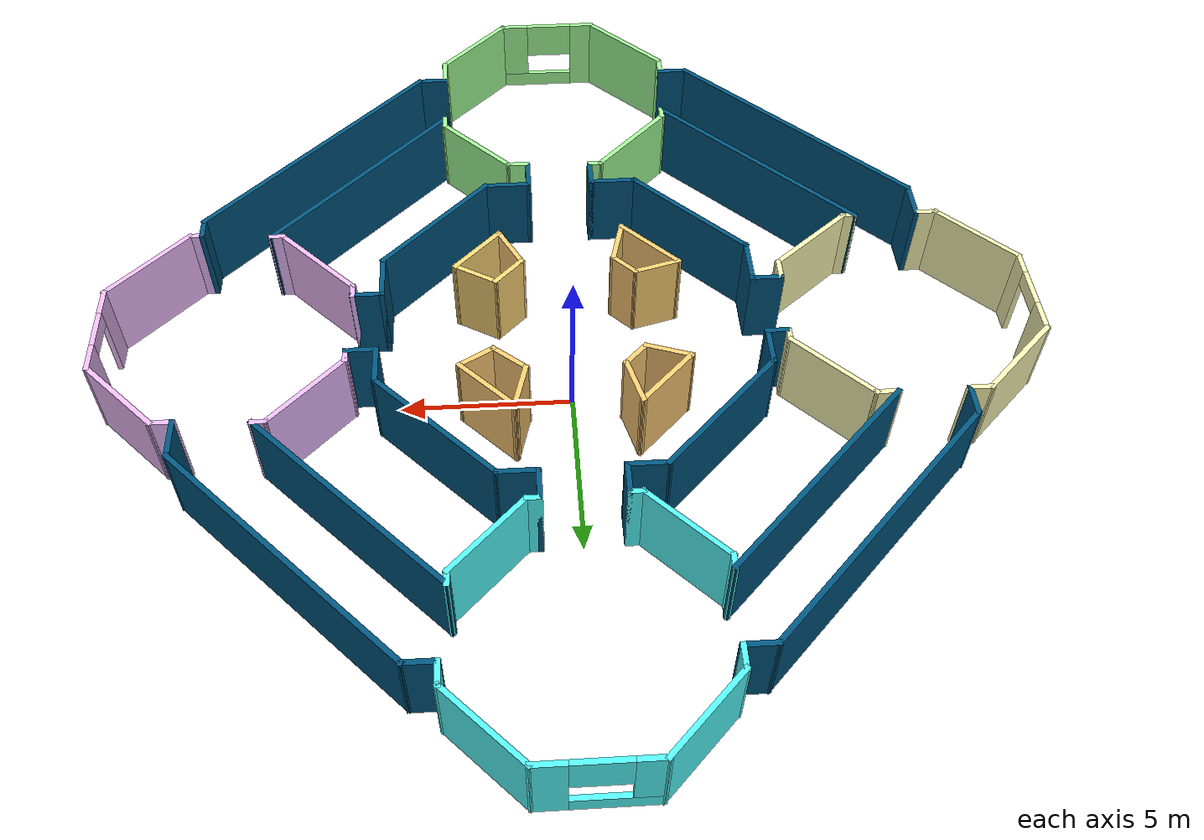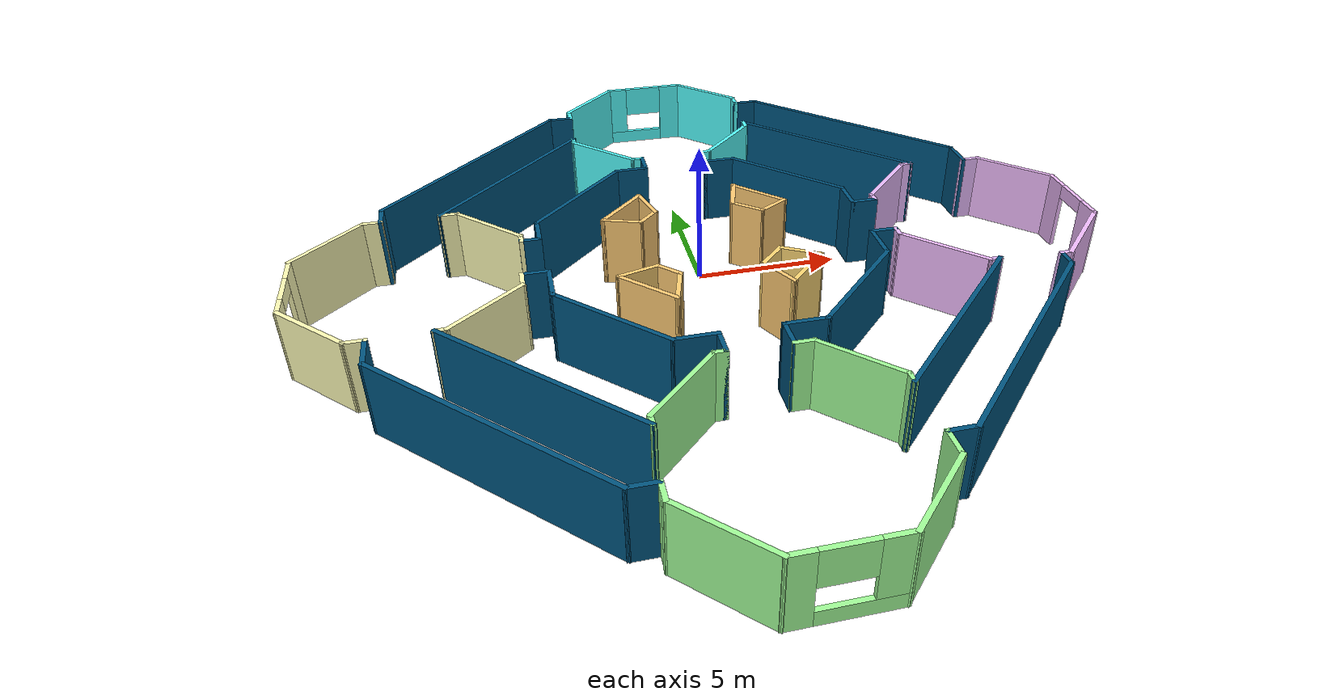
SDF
<?xml version='1.0'?>
<sdf version='1.6'>
  <model name='building'>
    <pose frame=''>-0.001846 -1.5065 0 0 -0 0</pose>
    <link name='Wall_0'>
      <collision name='Wall_0_Collision'>
        <geometry>
          <box>
            <size>2.25 0.15 2.5</size>
          </box>
        </geometry>
        <pose frame=''>0 0 1.25 0 -0 0</pose>
      </collision>
      <visual name='Wall_0_Visual'>
        <pose frame=''>0 0 1.25 0 -0 0</pose>
        <geometry>
          <box>
            <size>2.25 0.15 2.5</size>
          </box>
        </geometry>
        <material>
          <script>
            <uri>file://media/materials/scripts/gazebo.material</uri>
            <name>Gazebo/Grey</name>
          </script>
          <ambient>1 0.8 0.454902 1</ambient>
        </material>
        <meta>
          <layer>0</layer>
        </meta>
      </visual>
      <pose frame=''>-2.5367 2.70977 0 0 -0 0.785398</pose>
    </link>
    <link name='Wall_1'>
      <collision name='Wall_1_Collision'>
        <geometry>
          <box>
            <size>1.5 0.15 2.5</size>
          </box>
        </geometry>
        <pose frame=''>0 0 1.25 0 -0 0</pose>
      </collision>
      <visual name='Wall_1_Visual'>
        <pose frame=''>0 0 1.25 0 -0 0</pose>
        <geometry>
          <box>
            <size>1.5 0.15 2.5</size>
          </box>
        </geometry>
        <material>
          <script>
            <uri>file://media/materials/scripts/gazebo.material</uri>
            <name>Gazebo/Grey</name>
          </script>
          <ambient>1 0.8 0.454902 1</ambient>
        </material>
        <meta>
          <layer>0</layer>
        </meta>
      </visual>
      <pose frame=''>-1.61953 2.80023 0 0 0 -1.309</pose>
    </link>
    <link name='Wall_10'>
      <collision name='Wall_10_Collision'>
        <geometry>
          <box>
            <size>1.5 0.15 2.5</size>
          </box>
        </geometry>
        <pose frame=''>0 0 1.25 0 -0 0</pose>
      </collision>
      <visual name='Wall_10_Visual'>
        <pose frame=''>0 0 1.25 0 -0 0</pose>
        <geometry>
          <box>
            <size>1.5 0.15 2.5</size>
          </box>
        </geometry>
        <material>
          <script>
            <uri>file://media/materials/scripts/gazebo.material</uri>
            <name>Gazebo/Grey</name>
          </script>
          <ambient>1 0.819608 0.45098 1</ambient>
        </material>
        <meta>
          <layer>0</layer>
        </meta>
      </visual>
      <pose frame=''>-2.66214 -1.49592 0 0 -0 0.261799</pose>
    </link>
    <link name='Wall_100'>
      <collision name='Wall_100_Collision'>
        <geometry>
          <box>
            <size>0.75 0.15 2.5</size>
          </box>
        </geometry>
        <pose frame=''>0 0 1.25 0 -0 0</pose>
      </collision>
      <visual name='Wall_100_Visual'>
        <pose frame=''>0 0 1.25 0 -0 0</pose>
        <geometry>
          <box>
            <size>0.75 0.15 2.5</size>
          </box>
        </geometry>
        <material>
          <script>
            <uri>file://media/materials/scripts/gazebo.material</uri>
            <name>Gazebo/Grey</name>
          </script>
          <ambient>0.333333 1 1 1</ambient>
        </material>
        <meta>
          <layer>0</layer>
        </meta>
      </visual>
      <pose frame=''>3.70542 11.1499 0 0 -0 1.5708</pose>
    </link>
    <link name='Wall_101'>
      <collision name='Wall_101_Collision'>
        <geometry>
          <box>
            <size>3 0.15 2.5</size>
          </box>
        </geometry>
        <pose frame=''>0 0 1.25 0 -0 0</pose>
      </collision>
      <visual name='Wall_101_Visual'>
        <pose frame=''>0 0 1.25 0 -0 0</pose>
        <geometry>
          <box>
            <size>3 0.15 2.5</size>
          </box>
        </geometry>
        <material>
          <script>
            <uri>file://media/materials/scripts/gazebo.material</uri>
            <name>Gazebo/Grey</name>
          </script>
          <ambient>0.333333 1 1 1</ambient>
        </material>
        <meta>
          <layer>0</layer>
        </meta>
      </visual>
      <pose frame=''>2.69779 12.4576 0 0 -0 2.35619</pose>
    </link>
    <link name='Wall_102'>
      <pose frame=''>0.140165 13.4652 0 0 -0 3.14159</pose>
      <visual name='Wall_102_Visual_0'>
        <pose frame=''>-1.15171 0 1.25 0 -0 0</pose>
        <geometry>
          <box>
            <size>0.946574 0.15 2.5</size>
          </box>
        </geometry>
        <material>
          <script>
            <uri>file://media/materials/scripts/gazebo.material</uri>
            <name>Gazebo/Grey</name>
          </script>
          <ambient>0.333333 1 1 1</ambient>
        </material>
        <meta>
          <layer>0</layer>
        </meta>
      </visual>
      <collision name='Wall_102_Collision_0'>
        <geometry>
          <box>
            <size>0.946574 0.15 2.5</size>
          </box>
        </geometry>
        <pose frame=''>-1.15171 0 1.25 0 -0 0</pose>
      </collision>
      <visual name='Wall_102_Visual_1'>
        <pose frame=''>0.473287 0 0.25 0 -0 0</pose>
        <geometry>
          <box>
            <size>2.30343 0.15 0.5</size>
          </box>
        </geometry>
        <material>
          <script>
            <uri>file://media/materials/scripts/gazebo.material</uri>
            <name>Gazebo/Grey</name>
          </script>
          <ambient>0.333333 1 1 1</ambient>
        </material>
        <meta>
          <layer>0</layer>
        </meta>
      </visual>
      <collision name='Wall_102_Collision_1'>
        <geometry>
          <box>
            <size>2.30343 0.15 0.5</size>
          </box>
        </geometry>
        <pose frame=''>0.473287 0 0.25 0 -0 0</pose>
      </collision>
      <visual name='Wall_102_Visual_2'>
        <pose frame=''>1.22329 0 1.5 0 -0 0</pose>
        <geometry>
          <box>
            <size>0.803426 0.15 2</size>
          </box>
        </geometry>
        <material>
          <script>
            <uri>file://media/materials/scripts/gazebo.material</uri>
            <name>Gazebo/Grey</name>
          </script>
          <ambient>0.333333 1 1 1</ambient>
        </material>
        <meta>
          <layer>0</layer>
        </meta>
      </visual>
      <collision name='Wall_102_Collision_2'>
        <geometry>
          <box>
            <size>0.803426 0.15 2</size>
          </box>
        </geometry>
        <pose frame=''>1.22329 0 1.5 0 -0 0</pose>
      </collision>
      <visual name='Wall_102_Visual_3'>
        <pose frame=''>0.071574 0 1.9 0 -0 0</pose>
        <geometry>
          <box>
            <size>1.5 0.15 1.2</size>
          </box>
        </geometry>
        <material>
          <script>
            <uri>file://media/materials/scripts/gazebo.material</uri>
            <name>Gazebo/Grey</name>
          </script>
          <ambient>0.333333 1 1 1</ambient>
        </material>
        <meta>
          <layer>0</layer>
        </meta>
      </visual>
      <collision name='Wall_102_Collision_3'>
        <geometry>
          <box>
            <size>1.5 0.15 1.2</size>
          </box>
        </geometry>
        <pose frame=''>0.071574 0 1.9 0 -0 0</pose>
      </collision>
    </link>
    <link name='Wall_103'>
      <collision name='Wall_103_Collision'>
        <geometry>
          <box>
            <size>3 0.15 2.5</size>
          </box>
        </geometry>
        <pose frame=''>0 0 1.25 0 -0 0</pose>
      </collision>
      <visual name='Wall_103_Visual'>
        <pose frame=''>0 0 1.25 0 -0 0</pose>
        <geometry>
          <box>
            <size>3 0.15 2.5</size>
          </box>
        </geometry>
        <material>
          <script>
            <uri>file://media/materials/scripts/gazebo.material</uri>
            <name>Gazebo/Grey</name>
          </script>
          <ambient>0.333333 1 1 1</ambient>
        </material>
        <meta>
          <layer>0</layer>
        </meta>
      </visual>
      <pose frame=''>-2.41746 12.4576 0 0 0 -2.35619</pose>
    </link>
    <link name='Wall_104'>
      <collision name='Wall_104_Collision'>
        <geometry>
          <box>
            <size>0.75 0.15 2.5</size>
          </box>
        </geometry>
        <pose frame=''>0 0 1.25 0 -0 0</pose>
      </collision>
      <visual name='Wall_104_Visual'>
        <pose frame=''>0 0 1.25 0 -0 0</pose>
        <geometry>
          <box>
            <size>0.75 0.15 2.5</size>
          </box>
        </geometry>
        <material>
          <script>
            <uri>file://media/materials/scripts/gazebo.material</uri>
            <name>Gazebo/Grey</name>
          </script>
          <ambient>0.333333 1 1 1</ambient>
        </material>
        <meta>
          <layer>0</layer>
        </meta>
      </visual>
      <pose frame=''>-3.42509 11.1499 0 0 0 -1.5708</pose>
    </link>
    <link name='Wall_105'>
      <collision name='Wall_105_Collision'>
        <geometry>
          <box>
            <size>1 0.15 2.5</size>
          </box>
        </geometry>
        <pose frame=''>0 0 1.25 0 -0 0</pose>
      </collision>
      <visual name='Wall_105_Visual'>
        <pose frame=''>0 0 1.25 0 -0 0</pose>
        <geometry>
          <box>
            <size>1 0.15 2.5</size>
          </box>
        </geometry>
        <material>
          <script>
            <uri>file://media/materials/scripts/gazebo.material</uri>
            <name>Gazebo/Grey</name>
          </script>
          <ambient>0 0.333333 0.498039 1</ambient>
        </material>
        <meta>
          <layer>0</layer>
        </meta>
      </visual>
      <pose frame=''>-3.85009 10.8499 0 0 -0 3.14159</pose>
    </link>
    <link name='Wall_106'>
      <collision name='Wall_106_Collision'>
        <geometry>
          <box>
            <size>9.25 0.15 2.5</size>
          </box>
        </geometry>
        <pose frame=''>0 0 1.25 0 -0 0</pose>
      </collision>
      <visual name='Wall_106_Visual'>
        <pose frame=''>0 0 1.25 0 -0 0</pose>
        <geometry>
          <box>
            <size>9.25 0.15 2.5</size>
          </box>
        </geometry>
        <material>
          <script>
            <uri>file://media/materials/scripts/gazebo.material</uri>
            <name>Gazebo/Grey</name>
          </script>
          <ambient>0 0.333333 0.498039 1</ambient>
        </material>
        <meta>
          <layer>0</layer>
        </meta>
      </visual>
      <pose frame=''>-7.49242 7.63259 0 0 0 -2.35619</pose>
    </link>
    <link name='Wall_107'>
      <collision name='Wall_107_Collision'>
        <geometry>
          <box>
            <size>1 0.15 2.5</size>
          </box>
        </geometry>
        <pose frame=''>0 0 1.25 0 -0 0</pose>
      </collision>
      <visual name='Wall_107_Visual'>
        <pose frame=''>0 0 1.25 0 -0 0</pose>
        <geometry>
          <box>
            <size>1 0.15 2.5</size>
          </box>
        </geometry>
        <material>
          <script>
            <uri>file://media/materials/scripts/gazebo.material</uri>
            <name>Gazebo/Grey</name>
          </script>
          <ambient>0 0.333333 0.498039 1</ambient>
        </material>
        <meta>
          <layer>0</layer>
        </meta>
      </visual>
      <pose frame=''>-10.7098 3.99025 0 0 0 -1.5708</pose>
    </link>
    <link name='Wall_108'>
      <collision name='Wall_108_Collision'>
        <geometry>
          <box>
            <size>0.75 0.15 2.5</size>
          </box>
        </geometry>
        <pose frame=''>0 0 1.25 0 -0 0</pose>
      </collision>
      <visual name='Wall_108_Visual'>
        <pose frame=''>0 0 1.25 0 -0 0</pose>
        <geometry>
          <box>
            <size>0.75 0.15 2.5</size>
          </box>
        </geometry>
        <material>
          <script>
            <uri>file://media/materials/scripts/gazebo.material</uri>
            <name>Gazebo/Grey</name>
          </script>
          <ambient>1 0.992157 0.717647 1</ambient>
        </material>
        <meta>
          <layer>0</layer>
        </meta>
      </visual>
      <pose frame=''>-11.0098 3.56525 0 0 -0 3.14159</pose>
    </link>
    <link name='Wall_109'>
      <collision name='Wall_109_Collision'>
        <geometry>
          <box>
            <size>3.07414 0.15 2.5</size>
          </box>
        </geometry>
        <pose frame=''>0 0 1.25 0 -0 0</pose>
      </collision>
      <visual name='Wall_109_Visual'>
        <pose frame=''>0 0 1.25 0 -0 0</pose>
        <geometry>
          <box>
            <size>3.07414 0.15 2.5</size>
          </box>
        </geometry>
        <material>
          <script>
            <uri>file://media/materials/scripts/gazebo.material</uri>
            <name>Gazebo/Grey</name>
          </script>
          <ambient>1 0.992157 0.717647 1</ambient>
        </material>
        <meta>
          <layer>0</layer>
        </meta>
      </visual>
      <pose frame=''>-12.3692 2.55763 0 0 0 -2.38124</pose>
    </link>
    <link name='Wall_11'>
      <collision name='Wall_11_Collision'>
        <geometry>
          <box>
            <size>1 0.15 2.5</size>
          </box>
        </geometry>
        <pose frame=''>0 0 1.25 0 -0 0</pose>
      </collision>
      <visual name='Wall_11_Visual'>
        <pose frame=''>0 0 1.25 0 -0 0</pose>
        <geometry>
          <box>
            <size>1 0.15 2.5</size>
          </box>
        </geometry>
        <material>
          <script>
            <uri>file://media/materials/scripts/gazebo.material</uri>
            <name>Gazebo/Grey</name>
          </script>
          <ambient>1 0.8 0.454902 1</ambient>
        </material>
        <meta>
          <layer>0</layer>
        </meta>
      </visual>
      <pose frame=''>-1.70962 -1.62174 0 0 0 -0.785398</pose>
    </link>
    <link name='Wall_12'>
      <collision name='Wall_12_Collision'>
        <geometry>
          <box>
            <size>1.5 0.15 2.5</size>
          </box>
        </geometry>
        <pose frame=''>0 0 1.25 0 -0 0</pose>
      </collision>
      <visual name='Wall_12_Visual'>
        <pose frame=''>0 0 1.25 0 -0 0</pose>
        <geometry>
          <box>
            <size>1.5 0.15 2.5</size>
          </box>
        </geometry>
        <material>
          <script>
            <uri>file://media/materials/scripts/gazebo.material</uri>
            <name>Gazebo/Grey</name>
          </script>
          <ambient>1 0.819608 0.45098 1</ambient>
        </material>
        <meta>
          <layer>0</layer>
        </meta>
      </visual>
      <pose frame=''>-1.5838 -2.57426 0 0 0 -1.8326</pose>
    </link>
    <link name='Wall_13'>
      <collision name='Wall_13_Collision'>
        <geometry>
          <box>
            <size>2.35 0.15 2.5</size>
          </box>
        </geometry>
        <pose frame=''>0 0 1.25 0 -0 0</pose>
      </collision>
      <visual name='Wall_13_Visual'>
        <pose frame=''>0 0 1.25 0 -0 0</pose>
        <geometry>
          <box>
            <size>2.35 0.15 2.5</size>
          </box>
        </geometry>
        <material>
          <script>
            <uri>file://media/materials/scripts/gazebo.material</uri>
            <name>Gazebo/Grey</name>
          </script>
          <ambient>1 0.8 0.454902 1</ambient>
        </material>
        <meta>
          <layer>0</layer>
        </meta>
      </visual>
      <pose frame=''>-2.53633 -2.44844 0 0 -0 2.35619</pose>
    </link>
    <link name='Wall_15'>
      <collision name='Wall_15_Collision'>
        <geometry>
          <box>
            <size>1.25 0.15 2.5</size>
          </box>
        </geometry>
        <pose frame=''>0 0 1.25 0 -0 0</pose>
      </collision>
      <visual name='Wall_15_Visual'>
        <pose frame=''>0 0 1.25 0 -0 0</pose>
        <geometry>
          <box>
            <size>1.25 0.15 2.5</size>
          </box>
        </geometry>
        <material>
          <script>
            <uri>file://media/materials/scripts/gazebo.material</uri>
            <name>Gazebo/Grey</name>
          </script>
          <ambient>1 0.847059 0.458824 1</ambient>
        </material>
        <meta>
          <layer>0</layer>
        </meta>
      </visual>
      <pose frame=''>1.70963 -1.54407 0 0 -0 0.785398</pose>
    </link>
    <link name='Wall_16'>
      <collision name='Wall_16_Collision'>
        <geometry>
          <box>
            <size>1.5 0.15 2.5</size>
          </box>
        </geometry>
        <pose frame=''>0 0 1.25 0 -0 0</pose>
      </collision>
      <visual name='Wall_16_Visual'>
        <pose frame=''>0 0 1.25 0 -0 0</pose>
        <geometry>
          <box>
            <size>1.5 0.15 2.5</size>
          </box>
        </geometry>
        <material>
          <script>
            <uri>file://media/materials/scripts/gazebo.material</uri>
            <name>Gazebo/Grey</name>
          </script>
          <ambient>1 0.847059 0.458824 1</ambient>
        </material>
        <meta>
          <layer>0</layer>
        </meta>
      </visual>
      <pose frame=''>2.68311 -1.49266 0 0 0 -0.523599</pose>
    </link>
    <link name='Wall_17'>
      <collision name='Wall_17_Collision'>
        <geometry>
          <box>
            <size>2 0.15 2.5</size>
          </box>
        </geometry>
        <pose frame=''>0 0 1.25 0 -0 0</pose>
      </collision>
      <visual name='Wall_17_Visual'>
        <pose frame=''>0 0 1.25 0 -0 0</pose>
        <geometry>
          <box>
            <size>2 0.15 2.5</size>
          </box>
        </geometry>
        <material>
          <script>
            <uri>file://media/materials/scripts/gazebo.material</uri>
            <name>Gazebo/Grey</name>
          </script>
          <ambient>1 0.847059 0.458824 1</ambient>
        </material>
        <meta>
          <layer>0</layer>
        </meta>
      </visual>
      <pose frame=''>2.6136 -2.48423 0 0 0 -2.35619</pose>
    </link>
    <link name='Wall_18'>
      <collision name='Wall_18_Collision'>
        <geometry>
          <box>
            <size>1.51415 0.15 2.5</size>
          </box>
        </geometry>
        <pose frame=''>0 0 1.25 0 -0 0</pose>
      </collision>
      <visual name='Wall_18_Visual'>
        <pose frame=''>0 0 1.25 0 -0 0</pose>
        <geometry>
          <box>
            <size>1.51415 0.15 2.5</size>
          </box>
        </geometry>
        <material>
          <script>
            <uri>file://media/materials/scripts/gazebo.material</uri>
            <name>Gazebo/Grey</name>
          </script>
          <ambient>1 0.8 0.454902 1</ambient>
        </material>
        <meta>
          <layer>0</layer>
        </meta>
      </visual>
      <pose frame=''>1.64013 -2.53564 0 0 -0 2.05814</pose>
    </link>
    <link name='Wall_2'>
      <collision name='Wall_2_Collision'>
        <geometry>
          <box>
            <size>1 0.15 2.5</size>
          </box>
        </geometry>
        <pose frame=''>0 0 1.25 0 -0 0</pose>
      </collision>
      <visual name='Wall_2_Visual'>
        <pose frame=''>0 0 1.25 0 -0 0</pose>
        <geometry>
          <box>
            <size>1 0.15 2.5</size>
          </box>
        </geometry>
        <material>
          <script>
            <uri>file://media/materials/scripts/gazebo.material</uri>
            <name>Gazebo/Grey</name>
          </script>
          <ambient>1 0.8 0.454902 1</ambient>
        </material>
        <meta>
          <layer>0</layer>
        </meta>
      </visual>
      <pose frame=''>-1.74535 1.84771 0 0 0 -2.35619</pose>
    </link>
    <link name='Wall_20'>
      <collision name='Wall_20_Collision'>
        <geometry>
          <box>
            <size>1.5 0.15 2.5</size>
          </box>
        </geometry>
        <pose frame=''>0 0 1.25 0 -0 0</pose>
      </collision>
      <visual name='Wall_20_Visual'>
        <pose frame=''>0 0 1.25 0 -0 0</pose>
        <geometry>
          <box>
            <size>1.5 0.15 2.5</size>
          </box>
        </geometry>
        <material>
          <script>
            <uri>file://media/materials/scripts/gazebo.material</uri>
            <name>Gazebo/Grey</name>
          </script>
          <ambient>0 0.333333 0.498039 1</ambient>
        </material>
        <meta>
          <layer>0</layer>
        </meta>
      </visual>
      <pose frame=''>-5.40602 -1.52769 0 0 0 -1.5708</pose>
    </link>
    <link name='Wall_21'>
      <collision name='Wall_21_Collision'>
        <geometry>
          <box>
            <size>4.5 0.15 2.5</size>
          </box>
        </geometry>
        <pose frame=''>0 0 1.25 0 -0 0</pose>
      </collision>
      <visual name='Wall_21_Visual'>
        <pose frame=''>0 0 1.25 0 -0 0</pose>
        <geometry>
          <box>
            <size>4.5 0.15 2.5</size>
          </box>
        </geometry>
        <material>
          <script>
            <uri>file://media/materials/scripts/gazebo.material</uri>
            <name>Gazebo/Grey</name>
          </script>
          <ambient>0 0.333333 0.498039 1</ambient>
        </material>
        <meta>
          <layer>0</layer>
        </meta>
      </visual>
      <pose frame=''>-3.86807 -3.74065 0 0 0 -0.785398</pose>
    </link>
    <link name='Wall_22'>
      <collision name='Wall_22_Collision'>
        <geometry>
          <box>
            <size>1.5 0.15 2.5</size>
          </box>
        </geometry>
        <pose frame=''>0 0 1.25 0 -0 0</pose>
      </collision>
      <visual name='Wall_22_Visual'>
        <pose frame=''>0 0 1.25 0 -0 0</pose>
        <geometry>
          <box>
            <size>1.5 0.15 2.5</size>
          </box>
        </geometry>
        <material>
          <script>
            <uri>file://media/materials/scripts/gazebo.material</uri>
            <name>Gazebo/Grey</name>
          </script>
          <ambient>0 0.333333 0.498039 1</ambient>
        </material>
        <meta>
          <layer>0</layer>
        </meta>
      </visual>
      <pose frame=''>-1.65511 -5.2786 0 0 -0 0</pose>
    </link>
    <link name='Wall_23'>
      <collision name='Wall_23_Collision'>
        <geometry>
          <box>
            <size>1 0.15 2.5</size>
          </box>
        </geometry>
        <pose frame=''>0 0 1.25 0 -0 0</pose>
      </collision>
      <visual name='Wall_23_Visual'>
        <pose frame=''>0 0 1.25 0 -0 0</pose>
        <geometry>
          <box>
            <size>1 0.15 2.5</size>
          </box>
        </geometry>
        <material>
          <script>
            <uri>file://media/materials/scripts/gazebo.material</uri>
            <name>Gazebo/Grey</name>
          </script>
          <ambient>0 0.333333 0.498039 1</ambient>
        </material>
        <meta>
          <layer>0</layer>
        </meta>
      </visual>
      <pose frame=''>-0.980109 -5.7036 0 0 0 -1.5708</pose>
    </link>
    <link name='Wall_24'>
      <collision name='Wall_24_Collision'>
        <geometry>
          <box>
            <size>0.5 0.15 2.5</size>
          </box>
        </geometry>
        <pose frame=''>0 0 1.25 0 -0 0</pose>
      </collision>
      <visual name='Wall_24_Visual'>
        <pose frame=''>0 0 1.25 0 -0 0</pose>
        <geometry>
          <box>
            <size>0.5 0.15 2.5</size>
          </box>
        </geometry>
        <material>
          <script>
            <uri>file://media/materials/scripts/gazebo.material</uri>
            <name>Gazebo/Grey</name>
          </script>
          <ambient>0.639216 1 0.6 1</ambient>
        </material>
        <meta>
          <layer>0</layer>
        </meta>
      </visual>
      <pose frame=''>-1.15511 -6.1286 0 0 -0 3.14159</pose>
    </link>
    <link name='Wall_26'>
      <collision name='Wall_26_Collision'>
        <geometry>
          <box>
            <size>1 0.15 2.5</size>
          </box>
        </geometry>
        <pose frame=''>0 0 1.25 0 -0 0</pose>
      </collision>
      <visual name='Wall_26_Visual'>
        <pose frame=''>0 0 1.25 0 -0 0</pose>
        <geometry>
          <box>
            <size>1 0.15 2.5</size>
          </box>
        </geometry>
        <material>
          <script>
            <uri>file://media/materials/scripts/gazebo.material</uri>
            <name>Gazebo/Grey</name>
          </script>
          <ambient>0 0.333333 0.498039 1</ambient>
        </material>
        <meta>
          <layer>0</layer>
        </meta>
      </visual>
      <pose frame=''>-5.83102 -0.852688 0 0 -0 3.14159</pose>
    </link>
    <link name='Wall_27'>
      <collision name='Wall_27_Collision'>
        <geometry>
          <box>
            <size>0.75 0.15 2.5</size>
          </box>
        </geometry>
        <pose frame=''>0 0 1.25 0 -0 0</pose>
      </collision>
      <visual name='Wall_27_Visual'>
        <pose frame=''>0 0 1.25 0 -0 0</pose>
        <geometry>
          <box>
            <size>0.75 0.15 2.5</size>
          </box>
        </geometry>
        <material>
          <script>
            <uri>file://media/materials/scripts/gazebo.material</uri>
            <name>Gazebo/Grey</name>
          </script>
          <ambient>1 0.992157 0.717647 1</ambient>
        </material>
        <meta>
          <layer>0</layer>
        </meta>
      </visual>
      <pose frame=''>-6.25602 -1.15269 0 0 0 -1.5708</pose>
    </link>
    <link name='Wall_29'>
      <collision name='Wall_29_Collision'>
        <geometry>
          <box>
            <size>1.5 0.15 2.5</size>
          </box>
        </geometry>
        <pose frame=''>0 0 1.25 0 -0 0</pose>
      </collision>
      <visual name='Wall_29_Visual'>
        <pose frame=''>0 0 1.25 0 -0 0</pose>
        <geometry>
          <box>
            <size>1.5 0.15 2.5</size>
          </box>
        </geometry>
        <material>
          <script>
            <uri>file://media/materials/scripts/gazebo.material</uri>
            <name>Gazebo/Grey</name>
          </script>
          <ambient>0 0.333333 0.498039 1</ambient>
        </material>
        <meta>
          <layer>0</layer>
        </meta>
      </visual>
      <pose frame=''>1.65302 -5.27063 0 0 -0 0</pose>
    </link>
    <link name='Wall_3'>
      <collision name='Wall_3_Collision'>
        <geometry>
          <box>
            <size>1.45288 0.15 2.5</size>
          </box>
        </geometry>
        <pose frame=''>0 0 1.25 0 -0 0</pose>
      </collision>
      <visual name='Wall_3_Visual'>
        <pose frame=''>0 0 1.25 0 -0 0</pose>
        <geometry>
          <box>
            <size>1.45288 0.15 2.5</size>
          </box>
        </geometry>
        <material>
          <script>
            <uri>file://media/materials/scripts/gazebo.material</uri>
            <name>Gazebo/Grey</name>
          </script>
          <ambient>1 0.8 0.454902 1</ambient>
        </material>
        <meta>
          <layer>0</layer>
        </meta>
      </visual>
      <pose frame=''>-2.66252 1.75725 0 0 -0 2.81327</pose>
    </link>
    <link name='Wall_30'>
      <collision name='Wall_30_Collision'>
        <geometry>
          <box>
            <size>4.5 0.15 2.5</size>
          </box>
        </geometry>
        <pose frame=''>0 0 1.25 0 -0 0</pose>
      </collision>
      <visual name='Wall_30_Visual'>
        <pose frame=''>0 0 1.25 0 -0 0</pose>
        <geometry>
          <box>
            <size>4.5 0.15 2.5</size>
          </box>
        </geometry>
        <material>
          <script>
            <uri>file://media/materials/scripts/gazebo.material</uri>
            <name>Gazebo/Grey</name>
          </script>
          <ambient>0 0.333333 0.498039 1</ambient>
        </material>
        <meta>
          <layer>0</layer>
        </meta>
      </visual>
      <pose frame=''>3.86598 -3.73268 0 0 -0 0.785398</pose>
    </link>
    <link name='Wall_31'>
      <collision name='Wall_31_Collision'>
        <geometry>
          <box>
            <size>1.5 0.15 2.5</size>
          </box>
        </geometry>
        <pose frame=''>0 0 1.25 0 -0 0</pose>
      </collision>
      <visual name='Wall_31_Visual'>
        <pose frame=''>0 0 1.25 0 -0 0</pose>
        <geometry>
          <box>
            <size>1.5 0.15 2.5</size>
          </box>
        </geometry>
        <material>
          <script>
            <uri>file://media/materials/scripts/gazebo.material</uri>
            <name>Gazebo/Grey</name>
          </script>
          <ambient>0 0.333333 0.498039 1</ambient>
        </material>
        <meta>
          <layer>0</layer>
        </meta>
      </visual>
      <pose frame=''>5.40394 -1.51972 0 0 -0 1.5708</pose>
    </link>
    <link name='Wall_32'>
      <collision name='Wall_32_Collision'>
        <geometry>
          <box>
            <size>1 0.15 2.5</size>
          </box>
        </geometry>
        <pose frame=''>0 0 1.25 0 -0 0</pose>
      </collision>
      <visual name='Wall_32_Visual'>
        <pose frame=''>0 0 1.25 0 -0 0</pose>
        <geometry>
          <box>
            <size>1 0.15 2.5</size>
          </box>
        </geometry>
        <material>
          <script>
            <uri>file://media/materials/scripts/gazebo.material</uri>
            <name>Gazebo/Grey</name>
          </script>
          <ambient>0 0.333333 0.498039 1</ambient>
        </material>
        <meta>
          <layer>0</layer>
        </meta>
      </visual>
      <pose frame=''>5.82894 -0.84472 0 0 -0 0</pose>
    </link>
    <link name='Wall_33'>
      <collision name='Wall_33_Collision'>
        <geometry>
          <box>
            <size>0.5 0.15 2.5</size>
          </box>
        </geometry>
        <pose frame=''>0 0 1.25 0 -0 0</pose>
      </collision>
      <visual name='Wall_33_Visual'>
        <pose frame=''>0 0 1.25 0 -0 0</pose>
        <geometry>
          <box>
            <size>0.5 0.15 2.5</size>
          </box>
        </geometry>
        <material>
          <script>
            <uri>file://media/materials/scripts/gazebo.material</uri>
            <name>Gazebo/Grey</name>
          </script>
          <ambient>0.913725 0.737255 1 1</ambient>
        </material>
        <meta>
          <layer>0</layer>
        </meta>
      </visual>
      <pose frame=''>6.25394 -1.01972 0 0 0 -1.5708</pose>
    </link>
    <link name='Wall_35'>
      <collision name='Wall_35_Collision'>
        <geometry>
          <box>
            <size>0.5 0.15 2.5</size>
          </box>
        </geometry>
        <pose frame=''>0 0 1.25 0 -0 0</pose>
      </collision>
      <visual name='Wall_35_Visual'>
        <pose frame=''>0 0 1.25 0 -0 0</pose>
        <geometry>
          <box>
            <size>0.5 0.15 2.5</size>
          </box>
        </geometry>
        <material>
          <script>
            <uri>file://media/materials/scripts/gazebo.material</uri>
            <name>Gazebo/Grey</name>
          </script>
          <ambient>0.333333 1 1 1</ambient>
        </material>
        <meta>
          <layer>0</layer>
        </meta>
      </visual>
      <pose frame=''>1.3119 6.45658 0 0 -0 3.14159</pose>
    </link>
    <link name='Wall_36'>
      <collision name='Wall_36_Collision'>
        <geometry>
          <box>
            <size>1 0.15 2.5</size>
          </box>
        </geometry>
        <pose frame=''>0 0 1.25 0 -0 0</pose>
      </collision>
      <visual name='Wall_36_Visual'>
        <pose frame=''>0 0 1.25 0 -0 0</pose>
        <geometry>
          <box>
            <size>1 0.15 2.5</size>
          </box>
        </geometry>
        <material>
          <script>
            <uri>file://media/materials/scripts/gazebo.material</uri>
            <name>Gazebo/Grey</name>
          </script>
          <ambient>0 0.333333 0.498039 1</ambient>
        </material>
        <meta>
          <layer>0</layer>
        </meta>
      </visual>
      <pose frame=''>1.1369 6.03158 0 0 0 -1.5708</pose>
    </link>
    <link name='Wall_37'>
      <collision name='Wall_37_Collision'>
        <geometry>
          <box>
            <size>1.25 0.15 2.5</size>
          </box>
        </geometry>
        <pose frame=''>0 0 1.25 0 -0 0</pose>
      </collision>
      <visual name='Wall_37_Visual'>
        <pose frame=''>0 0 1.25 0 -0 0</pose>
        <geometry>
          <box>
            <size>1.25 0.15 2.5</size>
          </box>
        </geometry>
        <material>
          <script>
            <uri>file://media/materials/scripts/gazebo.material</uri>
            <name>Gazebo/Grey</name>
          </script>
          <ambient>0 0.333333 0.498039 1</ambient>
        </material>
        <meta>
          <layer>0</layer>
        </meta>
      </visual>
      <pose frame=''>1.6869 5.60658 0 0 -0 0</pose>
    </link>
    <link name='Wall_38'>
      <collision name='Wall_38_Collision'>
        <geometry>
          <box>
            <size>4.75 0.15 2.5</size>
          </box>
        </geometry>
        <pose frame=''>0 0 1.25 0 -0 0</pose>
      </collision>
      <visual name='Wall_38_Visual'>
        <pose frame=''>0 0 1.25 0 -0 0</pose>
        <geometry>
          <box>
            <size>4.75 0.15 2.5</size>
          </box>
        </geometry>
        <material>
          <script>
            <uri>file://media/materials/scripts/gazebo.material</uri>
            <name>Gazebo/Grey</name>
          </script>
          <ambient>0 0.333333 0.498039 1</ambient>
        </material>
        <meta>
          <layer>0</layer>
        </meta>
      </visual>
      <pose frame=''>3.86324 3.98024 0 0 0 -0.785398</pose>
    </link>
    <link name='Wall_39'>
      <collision name='Wall_39_Collision'>
        <geometry>
          <box>
            <size>1.25 0.15 2.5</size>
          </box>
        </geometry>
        <pose frame=''>0 0 1.25 0 -0 0</pose>
      </collision>
      <visual name='Wall_39_Visual'>
        <pose frame=''>0 0 1.25 0 -0 0</pose>
        <geometry>
          <box>
            <size>1.25 0.15 2.5</size>
          </box>
        </geometry>
        <material>
          <script>
            <uri>file://media/materials/scripts/gazebo.material</uri>
            <name>Gazebo/Grey</name>
          </script>
          <ambient>0 0.333333 0.498039 1</ambient>
        </material>
        <meta>
          <layer>0</layer>
        </meta>
      </visual>
      <pose frame=''>5.48959 1.80389 0 0 0 -1.5708</pose>
    </link>
    <link name='Wall_42'>
      <collision name='Wall_42_Collision'>
        <geometry>
          <box>
            <size>1 0.15 2.5</size>
          </box>
        </geometry>
        <pose frame=''>0 0 1.25 0 -0 0</pose>
      </collision>
      <visual name='Wall_42_Visual'>
        <pose frame=''>0 0 1.25 0 -0 0</pose>
        <geometry>
          <box>
            <size>1 0.15 2.5</size>
          </box>
        </geometry>
        <material>
          <script>
            <uri>file://media/materials/scripts/gazebo.material</uri>
            <name>Gazebo/Grey</name>
          </script>
          <ambient>0 0.333333 0.498039 1</ambient>
        </material>
        <meta>
          <layer>0</layer>
        </meta>
      </visual>
      <pose frame=''>5.91459 1.25389 0 0 -0 0</pose>
    </link>
    <link name='Wall_43'>
      <collision name='Wall_43_Collision'>
        <geometry>
          <box>
            <size>0.5 0.15 2.5</size>
          </box>
        </geometry>
        <pose frame=''>0 0 1.25 0 -0 0</pose>
      </collision>
      <visual name='Wall_43_Visual'>
        <pose frame=''>0 0 1.25 0 -0 0</pose>
        <geometry>
          <box>
            <size>0.5 0.15 2.5</size>
          </box>
        </geometry>
        <material>
          <script>
            <uri>file://media/materials/scripts/gazebo.material</uri>
            <name>Gazebo/Grey</name>
          </script>
          <ambient>0.913725 0.737255 1 1</ambient>
        </material>
        <meta>
          <layer>0</layer>
        </meta>
      </visual>
      <pose frame=''>6.33959 1.42889 0 0 -0 1.5708</pose>
    </link>
    <link name='Wall_45'>
      <collision name='Wall_45_Collision'>
        <geometry>
          <box>
            <size>0.5 0.15 2.5</size>
          </box>
        </geometry>
        <pose frame=''>0 0 1.25 0 -0 0</pose>
      </collision>
      <visual name='Wall_45_Visual'>
        <pose frame=''>0 0 1.25 0 -0 0</pose>
        <geometry>
          <box>
            <size>0.5 0.15 2.5</size>
          </box>
        </geometry>
        <material>
          <script>
            <uri>file://media/materials/scripts/gazebo.material</uri>
            <name>Gazebo/Grey</name>
          </script>
          <ambient>0.333333 1 1 1</ambient>
        </material>
        <meta>
          <layer>0</layer>
        </meta>
      </visual>
      <pose frame=''>-1.34508 6.41032 0 0 -0 0</pose>
    </link>
    <link name='Wall_46'>
      <collision name='Wall_46_Collision'>
        <geometry>
          <box>
            <size>1 0.15 2.5</size>
          </box>
        </geometry>
        <pose frame=''>0 0 1.25 0 -0 0</pose>
      </collision>
      <visual name='Wall_46_Visual'>
        <pose frame=''>0 0 1.25 0 -0 0</pose>
        <geometry>
          <box>
            <size>1 0.15 2.5</size>
          </box>
        </geometry>
        <material>
          <script>
            <uri>file://media/materials/scripts/gazebo.material</uri>
            <name>Gazebo/Grey</name>
          </script>
          <ambient>0 0.333333 0.498039 1</ambient>
        </material>
        <meta>
          <layer>0</layer>
        </meta>
      </visual>
      <pose frame=''>-1.17008 5.98532 0 0 0 -1.5708</pose>
    </link>
    <link name='Wall_47'>
      <collision name='Wall_47_Collision'>
        <geometry>
          <box>
            <size>1.25 0.15 2.5</size>
          </box>
        </geometry>
        <pose frame=''>0 0 1.25 0 -0 0</pose>
      </collision>
      <visual name='Wall_47_Visual'>
        <pose frame=''>0 0 1.25 0 -0 0</pose>
        <geometry>
          <box>
            <size>1.25 0.15 2.5</size>
          </box>
        </geometry>
        <material>
          <script>
            <uri>file://media/materials/scripts/gazebo.material</uri>
            <name>Gazebo/Grey</name>
          </script>
          <ambient>0 0.333333 0.498039 1</ambient>
        </material>
        <meta>
          <layer>0</layer>
        </meta>
      </visual>
      <pose frame=''>-1.72008 5.56032 0 0 -0 3.14159</pose>
    </link>
    <link name='Wall_48'>
      <collision name='Wall_48_Collision'>
        <geometry>
          <box>
            <size>4.75 0.15 2.5</size>
          </box>
        </geometry>
        <pose frame=''>0 0 1.25 0 -0 0</pose>
      </collision>
      <visual name='Wall_48_Visual'>
        <pose frame=''>0 0 1.25 0 -0 0</pose>
        <geometry>
          <box>
            <size>4.75 0.15 2.5</size>
          </box>
        </geometry>
        <material>
          <script>
            <uri>file://media/materials/scripts/gazebo.material</uri>
            <name>Gazebo/Grey</name>
          </script>
          <ambient>0 0.333333 0.498039 1</ambient>
        </material>
        <meta>
          <layer>0</layer>
        </meta>
      </visual>
      <pose frame=''>-3.89643 3.93398 0 0 0 -2.35619</pose>
    </link>
    <link name='Wall_49'>
      <collision name='Wall_49_Collision'>
        <geometry>
          <box>
            <size>1.25 0.15 2.5</size>
          </box>
        </geometry>
        <pose frame=''>0 0 1.25 0 -0 0</pose>
      </collision>
      <visual name='Wall_49_Visual'>
        <pose frame=''>0 0 1.25 0 -0 0</pose>
        <geometry>
          <box>
            <size>1.25 0.15 2.5</size>
          </box>
        </geometry>
        <material>
          <script>
            <uri>file://media/materials/scripts/gazebo.material</uri>
            <name>Gazebo/Grey</name>
          </script>
          <ambient>0 0.333333 0.498039 1</ambient>
        </material>
        <meta>
          <layer>0</layer>
        </meta>
      </visual>
      <pose frame=''>-5.52277 1.75763 0 0 0 -1.5708</pose>
    </link>
    <link name='Wall_5'>
      <collision name='Wall_5_Collision'>
        <geometry>
          <box>
            <size>1.5 0.15 2.5</size>
          </box>
        </geometry>
        <pose frame=''>0 0 1.25 0 -0 0</pose>
      </collision>
      <visual name='Wall_5_Visual'>
        <pose frame=''>0 0 1.25 0 -0 0</pose>
        <geometry>
          <box>
            <size>1.5 0.15 2.5</size>
          </box>
        </geometry>
        <material>
          <script>
            <uri>file://media/materials/scripts/gazebo.material</uri>
            <name>Gazebo/Grey</name>
          </script>
          <ambient>1 0.8 0.454902 1</ambient>
        </material>
        <meta>
          <layer>0</layer>
        </meta>
      </visual>
      <pose frame=''>1.51292 2.79421 0 0 -0 1.309</pose>
    </link>
    <link name='Wall_50'>
      <collision name='Wall_50_Collision'>
        <geometry>
          <box>
            <size>0.75 0.15 2.5</size>
          </box>
        </geometry>
        <pose frame=''>0 0 1.25 0 -0 0</pose>
      </collision>
      <visual name='Wall_50_Visual'>
        <pose frame=''>0 0 1.25 0 -0 0</pose>
        <geometry>
          <box>
            <size>0.75 0.15 2.5</size>
          </box>
        </geometry>
        <material>
          <script>
            <uri>file://media/materials/scripts/gazebo.material</uri>
            <name>Gazebo/Grey</name>
          </script>
          <ambient>0 0.333333 0.498039 1</ambient>
        </material>
        <meta>
          <layer>0</layer>
        </meta>
      </visual>
      <pose frame=''>-5.82277 1.20763 0 0 -0 3.14159</pose>
    </link>
    <link name='Wall_51'>
      <collision name='Wall_51_Collision'>
        <geometry>
          <box>
            <size>0.5 0.15 2.5</size>
          </box>
        </geometry>
        <pose frame=''>0 0 1.25 0 -0 0</pose>
      </collision>
      <visual name='Wall_51_Visual'>
        <pose frame=''>0 0 1.25 0 -0 0</pose>
        <geometry>
          <box>
            <size>0.5 0.15 2.5</size>
          </box>
        </geometry>
        <material>
          <script>
            <uri>file://media/materials/scripts/gazebo.material</uri>
            <name>Gazebo/Grey</name>
          </script>
          <ambient>1 0.992157 0.717647 1</ambient>
        </material>
        <meta>
          <layer>0</layer>
        </meta>
      </visual>
      <pose frame=''>-6.12277 1.38263 0 0 -0 1.5708</pose>
    </link>
    <link name='Wall_52'>
      <collision name='Wall_52_Collision'>
        <geometry>
          <box>
            <size>3 0.15 2.5</size>
          </box>
        </geometry>
        <pose frame=''>0 0 1.25 0 -0 0</pose>
      </collision>
      <visual name='Wall_52_Visual'>
        <pose frame=''>0 0 1.25 0 -0 0</pose>
        <geometry>
          <box>
            <size>3 0.15 2.5</size>
          </box>
        </geometry>
        <material>
          <script>
            <uri>file://media/materials/scripts/gazebo.material</uri>
            <name>Gazebo/Grey</name>
          </script>
          <ambient>1 0.992157 0.717647 1</ambient>
        </material>
        <meta>
          <layer>0</layer>
        </meta>
      </visual>
      <pose frame=''>-7.1304 2.56526 0 0 -0 2.35619</pose>
    </link>
    <link name='Wall_53'>
      <collision name='Wall_53_Collision'>
        <geometry>
          <box>
            <size>0.75 0.15 2.5</size>
          </box>
        </geometry>
        <pose frame=''>0 0 1.25 0 -0 0</pose>
      </collision>
      <visual name='Wall_53_Visual'>
        <pose frame=''>0 0 1.25 0 -0 0</pose>
        <geometry>
          <box>
            <size>0.75 0.15 2.5</size>
          </box>
        </geometry>
        <material>
          <script>
            <uri>file://media/materials/scripts/gazebo.material</uri>
            <name>Gazebo/Grey</name>
          </script>
          <ambient>1 0.992157 0.717647 1</ambient>
        </material>
        <meta>
          <layer>0</layer>
        </meta>
      </visual>
      <pose frame=''>-8.43803 3.57289 0 0 -0 3.14159</pose>
    </link>
    <link name='Wall_54'>
      <collision name='Wall_54_Collision'>
        <geometry>
          <box>
            <size>7.5 0.15 2.5</size>
          </box>
        </geometry>
        <pose frame=''>0 0 1.25 0 -0 0</pose>
      </collision>
      <visual name='Wall_54_Visual'>
        <pose frame=''>0 0 1.25 0 -0 0</pose>
        <geometry>
          <box>
            <size>7.5 0.15 2.5</size>
          </box>
        </geometry>
        <material>
          <script>
            <uri>file://media/materials/scripts/gazebo.material</uri>
            <name>Gazebo/Grey</name>
          </script>
          <ambient>0 0.333333 0.498039 1</ambient>
        </material>
        <meta>
          <layer>0</layer>
        </meta>
      </visual>
      <pose frame=''>-6.13941 6.1715 0 0 -0 0.785398</pose>
    </link>
    <link name='Wall_55'>
      <collision name='Wall_55_Collision'>
        <geometry>
          <box>
            <size>0.5 0.15 2.5</size>
          </box>
        </geometry>
        <pose frame=''>0 0 1.25 0 -0 0</pose>
      </collision>
      <visual name='Wall_55_Visual'>
        <pose frame=''>0 0 1.25 0 -0 0</pose>
        <geometry>
          <box>
            <size>0.5 0.15 2.5</size>
          </box>
        </geometry>
        <material>
          <script>
            <uri>file://media/materials/scripts/gazebo.material</uri>
            <name>Gazebo/Grey</name>
          </script>
          <ambient>0.333333 1 1 1</ambient>
        </material>
        <meta>
          <layer>0</layer>
        </meta>
      </visual>
      <pose frame=''>-3.54079 8.59512 0 0 0 -1.5708</pose>
    </link>
    <link name='Wall_56'>
      <collision name='Wall_56_Collision'>
        <geometry>
          <box>
            <size>3.00001 0.15 2.5</size>
          </box>
        </geometry>
        <pose frame=''>0 0 1.25 0 -0 0</pose>
      </collision>
      <visual name='Wall_56_Visual'>
        <pose frame=''>0 0 1.25 0 -0 0</pose>
        <geometry>
          <box>
            <size>3.00001 0.15 2.5</size>
          </box>
        </geometry>
        <material>
          <script>
            <uri>file://media/materials/scripts/gazebo.material</uri>
            <name>Gazebo/Grey</name>
          </script>
          <ambient>0.333333 1 1 1</ambient>
        </material>
        <meta>
          <layer>0</layer>
        </meta>
      </visual>
      <pose frame=''>-2.53044 7.41522 0 0 0 -0.782691</pose>
    </link>
    <link name='Wall_58'>
      <collision name='Wall_58_Collision'>
        <geometry>
          <box>
            <size>3 0.15 2.5</size>
          </box>
        </geometry>
        <pose frame=''>0 0 1.25 0 -0 0</pose>
      </collision>
      <visual name='Wall_58_Visual'>
        <pose frame=''>0 0 1.25 0 -0 0</pose>
        <geometry>
          <box>
            <size>3 0.15 2.5</size>
          </box>
        </geometry>
        <material>
          <script>
            <uri>file://media/materials/scripts/gazebo.material</uri>
            <name>Gazebo/Grey</name>
          </script>
          <ambient>0.333333 1 1 1</ambient>
        </material>
        <meta>
          <layer>0</layer>
        </meta>
      </visual>
      <pose frame=''>2.49452 7.46421 0 0 -0 0.785398</pose>
    </link>
    <link name='Wall_59'>
      <collision name='Wall_59_Collision'>
        <geometry>
          <box>
            <size>0.5 0.15 2.5</size>
          </box>
        </geometry>
        <pose frame=''>0 0 1.25 0 -0 0</pose>
      </collision>
      <visual name='Wall_59_Visual'>
        <pose frame=''>0 0 1.25 0 -0 0</pose>
        <geometry>
          <box>
            <size>0.5 0.15 2.5</size>
          </box>
        </geometry>
        <material>
          <script>
            <uri>file://media/materials/scripts/gazebo.material</uri>
            <name>Gazebo/Grey</name>
          </script>
          <ambient>0.333333 1 1 1</ambient>
        </material>
        <meta>
          <layer>0</layer>
        </meta>
      </visual>
      <pose frame=''>3.50215 8.64684 0 0 -0 1.5708</pose>
    </link>
    <link name='Wall_6'>
      <collision name='Wall_6_Collision'>
        <geometry>
          <box>
            <size>2.25 0.15 2.5</size>
          </box>
        </geometry>
        <pose frame=''>0 0 1.25 0 -0 0</pose>
      </collision>
      <visual name='Wall_6_Visual'>
        <pose frame=''>0 0 1.25 0 -0 0</pose>
        <geometry>
          <box>
            <size>2.25 0.15 2.5</size>
          </box>
        </geometry>
        <material>
          <script>
            <uri>file://media/materials/scripts/gazebo.material</uri>
            <name>Gazebo/Grey</name>
          </script>
          <ambient>1 0.8 0.454902 1</ambient>
        </material>
        <meta>
          <layer>0</layer>
        </meta>
      </visual>
      <pose frame=''>2.43008 2.70375 0 0 0 -0.785398</pose>
    </link>
    <link name='Wall_60'>
      <collision name='Wall_60_Collision'>
        <geometry>
          <box>
            <size>7.5 0.15 2.5</size>
          </box>
        </geometry>
        <pose frame=''>0 0 1.25 0 -0 0</pose>
      </collision>
      <visual name='Wall_60_Visual'>
        <pose frame=''>0 0 1.25 0 -0 0</pose>
        <geometry>
          <box>
            <size>7.5 0.15 2.5</size>
          </box>
        </geometry>
        <material>
          <script>
            <uri>file://media/materials/scripts/gazebo.material</uri>
            <name>Gazebo/Grey</name>
          </script>
          <ambient>0 0.333333 0.498039 1</ambient>
        </material>
        <meta>
          <layer>0</layer>
        </meta>
      </visual>
      <pose frame=''>6.10077 6.22322 0 0 0 -0.785398</pose>
    </link>
    <link name='Wall_61'>
      <collision name='Wall_61_Collision'>
        <geometry>
          <box>
            <size>0.5 0.15 2.5</size>
          </box>
        </geometry>
        <pose frame=''>0 0 1.25 0 -0 0</pose>
      </collision>
      <visual name='Wall_61_Visual'>
        <pose frame=''>0 0 1.25 0 -0 0</pose>
        <geometry>
          <box>
            <size>0.5 0.15 2.5</size>
          </box>
        </geometry>
        <material>
          <script>
            <uri>file://media/materials/scripts/gazebo.material</uri>
            <name>Gazebo/Grey</name>
          </script>
          <ambient>0.913725 0.737255 1 1</ambient>
        </material>
        <meta>
          <layer>0</layer>
        </meta>
      </visual>
      <pose frame=''>8.52439 3.6246 0 0 -0 3.14159</pose>
    </link>
    <link name='Wall_62'>
      <collision name='Wall_62_Collision'>
        <geometry>
          <box>
            <size>3.00001 0.15 2.5</size>
          </box>
        </geometry>
        <pose frame=''>0 0 1.25 0 -0 0</pose>
      </collision>
      <visual name='Wall_62_Visual'>
        <pose frame=''>0 0 1.25 0 -0 0</pose>
        <geometry>
          <box>
            <size>3.00001 0.15 2.5</size>
          </box>
        </geometry>
        <material>
          <script>
            <uri>file://media/materials/scripts/gazebo.material</uri>
            <name>Gazebo/Grey</name>
          </script>
          <ambient>0.913725 0.737255 1 1</ambient>
        </material>
        <meta>
          <layer>0</layer>
        </meta>
      </visual>
      <pose frame=''>7.34449 2.61425 0 0 0 -2.35349</pose>
    </link>
    <link name='Wall_64'>
      <collision name='Wall_64_Collision'>
        <geometry>
          <box>
            <size>3.25 0.15 2.5</size>
          </box>
        </geometry>
        <pose frame=''>0 0 1.25 0 -0 0</pose>
      </collision>
      <visual name='Wall_64_Visual'>
        <pose frame=''>0 0 1.25 0 -0 0</pose>
        <geometry>
          <box>
            <size>3.25 0.15 2.5</size>
          </box>
        </geometry>
        <material>
          <script>
            <uri>file://media/materials/scripts/gazebo.material</uri>
            <name>Gazebo/Grey</name>
          </script>
          <ambient>0.94902 0.741176 1 1</ambient>
        </material>
        <meta>
          <layer>0</layer>
        </meta>
      </visual>
      <pose frame=''>7.34995 -2.29074 0 0 0 -0.785398</pose>
    </link>
    <link name='Wall_65'>
      <collision name='Wall_65_Collision'>
        <geometry>
          <box>
            <size>0.5 0.15 2.5</size>
          </box>
        </geometry>
        <pose frame=''>0 0 1.25 0 -0 0</pose>
      </collision>
      <visual name='Wall_65_Visual'>
        <pose frame=''>0 0 1.25 0 -0 0</pose>
        <geometry>
          <box>
            <size>0.5 0.15 2.5</size>
          </box>
        </geometry>
        <material>
          <script>
            <uri>file://media/materials/scripts/gazebo.material</uri>
            <name>Gazebo/Grey</name>
          </script>
          <ambient>0.913725 0.737255 1 1</ambient>
        </material>
        <meta>
          <layer>0</layer>
        </meta>
      </visual>
      <pose frame=''>8.62097 -3.38675 0 0 -0 0</pose>
    </link>
    <link name='Wall_66'>
      <collision name='Wall_66_Collision'>
        <geometry>
          <box>
            <size>7.5 0.15 2.5</size>
          </box>
        </geometry>
        <pose frame=''>0 0 1.25 0 -0 0</pose>
      </collision>
      <visual name='Wall_66_Visual'>
        <pose frame=''>0 0 1.25 0 -0 0</pose>
        <geometry>
          <box>
            <size>7.5 0.15 2.5</size>
          </box>
        </geometry>
        <material>
          <script>
            <uri>file://media/materials/scripts/gazebo.material</uri>
            <name>Gazebo/Grey</name>
          </script>
          <ambient>0 0.333333 0.498039 1</ambient>
        </material>
        <meta>
          <layer>0</layer>
        </meta>
      </visual>
      <pose frame=''>6.19735 -5.98537 0 0 0 -2.35619</pose>
    </link>
    <link name='Wall_67'>
      <collision name='Wall_67_Collision'>
        <geometry>
          <box>
            <size>0.5 0.15 2.5</size>
          </box>
        </geometry>
        <pose frame=''>0 0 1.25 0 -0 0</pose>
      </collision>
      <visual name='Wall_67_Visual'>
        <pose frame=''>0 0 1.25 0 -0 0</pose>
        <geometry>
          <box>
            <size>0.5 0.15 2.5</size>
          </box>
        </geometry>
        <material>
          <script>
            <uri>file://media/materials/scripts/gazebo.material</uri>
            <name>Gazebo/Grey</name>
          </script>
          <ambient>0.639216 1 0.6 1</ambient>
        </material>
        <meta>
          <layer>0</layer>
        </meta>
      </visual>
      <pose frame=''>3.59874 -8.40899 0 0 -0 1.5708</pose>
    </link>
    <link name='Wall_68'>
      <collision name='Wall_68_Collision'>
        <geometry>
          <box>
            <size>3 0.15 2.5</size>
          </box>
        </geometry>
        <pose frame=''>0 0 1.25 0 -0 0</pose>
      </collision>
      <visual name='Wall_68_Visual'>
        <pose frame=''>0 0 1.25 0 -0 0</pose>
        <geometry>
          <box>
            <size>3 0.15 2.5</size>
          </box>
        </geometry>
        <material>
          <script>
            <uri>file://media/materials/scripts/gazebo.material</uri>
            <name>Gazebo/Grey</name>
          </script>
          <ambient>0.639216 1 0.6 1</ambient>
        </material>
        <meta>
          <layer>0</layer>
        </meta>
      </visual>
      <pose frame=''>2.59111 -7.22636 0 0 -0 2.35619</pose>
    </link>
    <link name='Wall_69'>
      <collision name='Wall_69_Collision'>
        <geometry>
          <box>
            <size>0.75 0.15 2.5</size>
          </box>
        </geometry>
        <pose frame=''>0 0 1.25 0 -0 0</pose>
      </collision>
      <visual name='Wall_69_Visual'>
        <pose frame=''>0 0 1.25 0 -0 0</pose>
        <geometry>
          <box>
            <size>0.75 0.15 2.5</size>
          </box>
        </geometry>
        <material>
          <script>
            <uri>file://media/materials/scripts/gazebo.material</uri>
            <name>Gazebo/Grey</name>
          </script>
          <ambient>0.639216 1 0.6 1</ambient>
        </material>
        <meta>
          <layer>0</layer>
        </meta>
      </visual>
      <pose frame=''>1.28348 -6.21873 0 0 -0 3.14159</pose>
    </link>
    <link name='Wall_7'>
      <collision name='Wall_7_Collision'>
        <geometry>
          <box>
            <size>1.25 0.15 2.5</size>
          </box>
        </geometry>
        <pose frame=''>0 0 1.25 0 -0 0</pose>
      </collision>
      <visual name='Wall_7_Visual'>
        <pose frame=''>0 0 1.25 0 -0 0</pose>
        <geometry>
          <box>
            <size>1.25 0.15 2.5</size>
          </box>
        </geometry>
        <material>
          <script>
            <uri>file://media/materials/scripts/gazebo.material</uri>
            <name>Gazebo/Grey</name>
          </script>
          <ambient>1 0.8 0.454902 1</ambient>
        </material>
        <meta>
          <layer>0</layer>
        </meta>
      </visual>
      <pose frame=''>2.69623 1.68628 0 0 0 -2.61799</pose>
    </link>
    <link name='Wall_70'>
      <collision name='Wall_70_Collision'>
        <geometry>
          <box>
            <size>1.09811 0.15 2.5</size>
          </box>
        </geometry>
        <pose frame=''>0 0 1.25 0 -0 0</pose>
      </collision>
      <visual name='Wall_70_Visual'>
        <pose frame=''>0 0 1.25 0 -0 0</pose>
        <geometry>
          <box>
            <size>1.09811 0.15 2.5</size>
          </box>
        </geometry>
        <material>
          <script>
            <uri>file://media/materials/scripts/gazebo.material</uri>
            <name>Gazebo/Grey</name>
          </script>
          <ambient>0 0.333333 0.498039 1</ambient>
        </material>
        <meta>
          <layer>0</layer>
        </meta>
      </visual>
      <pose frame=''>0.980752 -5.74468 0 0 -0 1.57655</pose>
    </link>
    <link name='Wall_72'>
      <collision name='Wall_72_Collision'>
        <geometry>
          <box>
            <size>3.25 0.15 2.5</size>
          </box>
        </geometry>
        <pose frame=''>0 0 1.25 0 -0 0</pose>
      </collision>
      <visual name='Wall_72_Visual'>
        <pose frame=''>0 0 1.25 0 -0 0</pose>
        <geometry>
          <box>
            <size>3.25 0.15 2.5</size>
          </box>
        </geometry>
        <material>
          <script>
            <uri>file://media/materials/scripts/gazebo.material</uri>
            <name>Gazebo/Grey</name>
          </script>
          <ambient>0.639216 1 0.6 1</ambient>
        </material>
        <meta>
          <layer>0</layer>
        </meta>
      </visual>
      <pose frame=''>-2.42612 -7.22462 0 0 0 -2.35619</pose>
    </link>
    <link name='Wall_73'>
      <collision name='Wall_73_Collision'>
        <geometry>
          <box>
            <size>0.5 0.15 2.5</size>
          </box>
        </geometry>
        <pose frame=''>0 0 1.25 0 -0 0</pose>
      </collision>
      <visual name='Wall_73_Visual'>
        <pose frame=''>0 0 1.25 0 -0 0</pose>
        <geometry>
          <box>
            <size>0.5 0.15 2.5</size>
          </box>
        </geometry>
        <material>
          <script>
            <uri>file://media/materials/scripts/gazebo.material</uri>
            <name>Gazebo/Grey</name>
          </script>
          <ambient>0.639216 1 0.6 1</ambient>
        </material>
        <meta>
          <layer>0</layer>
        </meta>
      </visual>
      <pose frame=''>-3.52214 -8.49563 0 0 0 -1.5708</pose>
    </link>
    <link name='Wall_74'>
      <collision name='Wall_74_Collision'>
        <geometry>
          <box>
            <size>7.75 0.15 2.5</size>
          </box>
        </geometry>
        <pose frame=''>0 0 1.25 0 -0 0</pose>
      </collision>
      <visual name='Wall_74_Visual'>
        <pose frame=''>0 0 1.25 0 -0 0</pose>
        <geometry>
          <box>
            <size>7.75 0.15 2.5</size>
          </box>
        </geometry>
        <material>
          <script>
            <uri>file://media/materials/scripts/gazebo.material</uri>
            <name>Gazebo/Grey</name>
          </script>
          <ambient>0 0.333333 0.498039 1</ambient>
        </material>
        <meta>
          <layer>0</layer>
        </meta>
      </visual>
      <pose frame=''>-6.20915 -5.98363 0 0 -0 2.35619</pose>
    </link>
    <link name='Wall_75'>
      <collision name='Wall_75_Collision'>
        <geometry>
          <box>
            <size>0.5 0.15 2.5</size>
          </box>
        </geometry>
        <pose frame=''>0 0 1.25 0 -0 0</pose>
      </collision>
      <visual name='Wall_75_Visual'>
        <pose frame=''>0 0 1.25 0 -0 0</pose>
        <geometry>
          <box>
            <size>0.5 0.15 2.5</size>
          </box>
        </geometry>
        <material>
          <script>
            <uri>file://media/materials/scripts/gazebo.material</uri>
            <name>Gazebo/Grey</name>
          </script>
          <ambient>1 0.992157 0.717647 1</ambient>
        </material>
        <meta>
          <layer>0</layer>
        </meta>
      </visual>
      <pose frame=''>-8.72115 -3.29662 0 0 -0 0</pose>
    </link>
    <link name='Wall_76'>
      <collision name='Wall_76_Collision'>
        <geometry>
          <box>
            <size>3.0902 0.15 2.5</size>
          </box>
        </geometry>
        <pose frame=''>0 0 1.25 0 -0 0</pose>
      </collision>
      <visual name='Wall_76_Visual'>
        <pose frame=''>0 0 1.25 0 -0 0</pose>
        <geometry>
          <box>
            <size>3.0902 0.15 2.5</size>
          </box>
        </geometry>
        <material>
          <script>
            <uri>file://media/materials/scripts/gazebo.material</uri>
            <name>Gazebo/Grey</name>
          </script>
          <ambient>1 0.992157 0.717647 1</ambient>
        </material>
        <meta>
          <layer>0</layer>
        </meta>
      </visual>
      <pose frame=''>-7.40109 -2.37466 0 0 -0 0.677883</pose>
    </link>
    <link name='Wall_78'>
      <pose frame=''>-13.4286 0.125 0 0 0 -1.5708</pose>
      <visual name='Wall_78_Visual_0'>
        <pose frame=''>-0.988376 0 1.25 0 -0 0</pose>
        <geometry>
          <box>
            <size>1.02325 0.15 2.5</size>
          </box>
        </geometry>
        <material>
          <script>
            <uri>file://media/materials/scripts/gazebo.material</uri>
            <name>Gazebo/Grey</name>
          </script>
          <ambient>1 0.992157 0.717647 1</ambient>
        </material>
        <meta>
          <layer>0</layer>
        </meta>
      </visual>
      <collision name='Wall_78_Collision_0'>
        <geometry>
          <box>
            <size>1.02325 0.15 2.5</size>
          </box>
        </geometry>
        <pose frame=''>-0.988376 0 1.25 0 -0 0</pose>
      </collision>
      <visual name='Wall_78_Visual_1'>
        <pose frame=''>1.11162 0 1.25 0 -0 0</pose>
        <geometry>
          <box>
            <size>0.776753 0.15 2.5</size>
          </box>
        </geometry>
        <material>
          <script>
            <uri>file://media/materials/scripts/gazebo.material</uri>
            <name>Gazebo/Grey</name>
          </script>
          <ambient>1 0.992157 0.717647 1</ambient>
        </material>
        <meta>
          <layer>0</layer>
        </meta>
      </visual>
      <collision name='Wall_78_Collision_1'>
        <geometry>
          <box>
            <size>0.776753 0.15 2.5</size>
          </box>
        </geometry>
        <pose frame=''>1.11162 0 1.25 0 -0 0</pose>
      </collision>
      <visual name='Wall_78_Visual_2'>
        <pose frame=''>0.123247 0 2.25 0 -0 0</pose>
        <geometry>
          <box>
            <size>1.2 0.15 0.5</size>
          </box>
        </geometry>
        <material>
          <script>
            <uri>file://media/materials/scripts/gazebo.material</uri>
            <name>Gazebo/Grey</name>
          </script>
          <ambient>1 0.992157 0.717647 1</ambient>
        </material>
        <meta>
          <layer>0</layer>
        </meta>
      </visual>
      <collision name='Wall_78_Collision_2'>
        <geometry>
          <box>
            <size>1.2 0.15 0.5</size>
          </box>
        </geometry>
        <pose frame=''>0.123247 0 2.25 0 -0 0</pose>
      </collision>
    </link>
    <link name='Wall_79'>
      <collision name='Wall_79_Collision'>
        <geometry>
          <box>
            <size>3 0.15 2.5</size>
          </box>
        </geometry>
        <pose frame=''>0 0 1.25 0 -0 0</pose>
      </collision>
      <visual name='Wall_79_Visual'>
        <pose frame=''>0 0 1.25 0 -0 0</pose>
        <geometry>
          <box>
            <size>3 0.15 2.5</size>
          </box>
        </geometry>
        <material>
          <script>
            <uri>file://media/materials/scripts/gazebo.material</uri>
            <name>Gazebo/Grey</name>
          </script>
          <ambient>1 0.992157 0.717647 1</ambient>
        </material>
        <meta>
          <layer>0</layer>
        </meta>
      </visual>
      <pose frame=''>-12.4209 -2.30763 0 0 0 -0.785398</pose>
    </link>
    <link name='Wall_8'>
      <collision name='Wall_8_Collision'>
        <geometry>
          <box>
            <size>1.29527 0.15 2.5</size>
          </box>
        </geometry>
        <pose frame=''>0 0 1.25 0 -0 0</pose>
      </collision>
      <visual name='Wall_8_Visual'>
        <pose frame=''>0 0 1.25 0 -0 0</pose>
        <geometry>
          <box>
            <size>1.29527 0.15 2.5</size>
          </box>
        </geometry>
        <material>
          <script>
            <uri>file://media/materials/scripts/gazebo.material</uri>
            <name>Gazebo/Grey</name>
          </script>
          <ambient>1 0.8 0.454902 1</ambient>
        </material>
        <meta>
          <layer>0</layer>
        </meta>
      </visual>
      <pose frame=''>1.77906 1.77675 0 0 -0 2.44942</pose>
    </link>
    <link name='Wall_80'>
      <collision name='Wall_80_Collision'>
        <geometry>
          <box>
            <size>0.75 0.15 2.5</size>
          </box>
        </geometry>
        <pose frame=''>0 0 1.25 0 -0 0</pose>
      </collision>
      <visual name='Wall_80_Visual'>
        <pose frame=''>0 0 1.25 0 -0 0</pose>
        <geometry>
          <box>
            <size>0.75 0.15 2.5</size>
          </box>
        </geometry>
        <material>
          <script>
            <uri>file://media/materials/scripts/gazebo.material</uri>
            <name>Gazebo/Grey</name>
          </script>
          <ambient>1 0.992157 0.717647 1</ambient>
        </material>
        <meta>
          <layer>0</layer>
        </meta>
      </visual>
      <pose frame=''>-11.1133 -3.31526 0 0 -0 0</pose>
    </link>
    <link name='Wall_81'>
      <collision name='Wall_81_Collision'>
        <geometry>
          <box>
            <size>1.25 0.15 2.5</size>
          </box>
        </geometry>
        <pose frame=''>0 0 1.25 0 -0 0</pose>
      </collision>
      <visual name='Wall_81_Visual'>
        <pose frame=''>0 0 1.25 0 -0 0</pose>
        <geometry>
          <box>
            <size>1.25 0.15 2.5</size>
          </box>
        </geometry>
        <material>
          <script>
            <uri>file://media/materials/scripts/gazebo.material</uri>
            <name>Gazebo/Grey</name>
          </script>
          <ambient>0 0.333333 0.498039 1</ambient>
        </material>
        <meta>
          <layer>0</layer>
        </meta>
      </visual>
      <pose frame=''>-10.8133 -3.86525 0 0 0 -1.5708</pose>
    </link>
    <link name='Wall_82'>
      <collision name='Wall_82_Collision'>
        <geometry>
          <box>
            <size>9 0.15 2.5</size>
          </box>
        </geometry>
        <pose frame=''>0 0 1.25 0 -0 0</pose>
      </collision>
      <visual name='Wall_82_Visual'>
        <pose frame=''>0 0 1.25 0 -0 0</pose>
        <geometry>
          <box>
            <size>9 0.15 2.5</size>
          </box>
        </geometry>
        <material>
          <script>
            <uri>file://media/materials/scripts/gazebo.material</uri>
            <name>Gazebo/Grey</name>
          </script>
          <ambient>0 0.333333 0.498039 1</ambient>
        </material>
        <meta>
          <layer>0</layer>
        </meta>
      </visual>
      <pose frame=''>-7.68437 -7.5442 0 0 0 -0.785398</pose>
    </link>
    <link name='Wall_83'>
      <collision name='Wall_83_Collision'>
        <geometry>
          <box>
            <size>1 0.15 2.5</size>
          </box>
        </geometry>
        <pose frame=''>0 0 1.25 0 -0 0</pose>
      </collision>
      <visual name='Wall_83_Visual'>
        <pose frame=''>0 0 1.25 0 -0 0</pose>
        <geometry>
          <box>
            <size>1 0.15 2.5</size>
          </box>
        </geometry>
        <material>
          <script>
            <uri>file://media/materials/scripts/gazebo.material</uri>
            <name>Gazebo/Grey</name>
          </script>
          <ambient>0 0.333333 0.498039 1</ambient>
        </material>
        <meta>
          <layer>0</layer>
        </meta>
      </visual>
      <pose frame=''>-4.13042 -10.6731 0 0 -0 0</pose>
    </link>
    <link name='Wall_84'>
      <collision name='Wall_84_Collision'>
        <geometry>
          <box>
            <size>0.75 0.15 2.5</size>
          </box>
        </geometry>
        <pose frame=''>0 0 1.25 0 -0 0</pose>
      </collision>
      <visual name='Wall_84_Visual'>
        <pose frame=''>0 0 1.25 0 -0 0</pose>
        <geometry>
          <box>
            <size>0.75 0.15 2.5</size>
          </box>
        </geometry>
        <material>
          <script>
            <uri>file://media/materials/scripts/gazebo.material</uri>
            <name>Gazebo/Grey</name>
          </script>
          <ambient>0.639216 1 0.6 1</ambient>
        </material>
        <meta>
          <layer>0</layer>
        </meta>
      </visual>
      <pose frame=''>-3.70542 -10.9732 0 0 0 -1.5708</pose>
    </link>
    <link name='Wall_85'>
      <collision name='Wall_85_Collision'>
        <geometry>
          <box>
            <size>3.25 0.15 2.5</size>
          </box>
        </geometry>
        <pose frame=''>0 0 1.25 0 -0 0</pose>
      </collision>
      <visual name='Wall_85_Visual'>
        <pose frame=''>0 0 1.25 0 -0 0</pose>
        <geometry>
          <box>
            <size>3.25 0.15 2.5</size>
          </box>
        </geometry>
        <material>
          <script>
            <uri>file://media/materials/scripts/gazebo.material</uri>
            <name>Gazebo/Grey</name>
          </script>
          <ambient>0.639216 1 0.6 1</ambient>
        </material>
        <meta>
          <layer>0</layer>
        </meta>
      </visual>
      <pose frame=''>-2.6094 -12.3692 0 0 0 -0.785398</pose>
    </link>
    <link name='Wall_86'>
      <pose frame=''>0.036612 -13.4652 0 0 -0 0</pose>
      <visual name='Wall_86_Visual_0'>
        <pose frame=''>-1.2173 0 1.25 0 -0 0</pose>
        <geometry>
          <box>
            <size>0.815405 0.15 2.5</size>
          </box>
        </geometry>
        <material>
          <script>
            <uri>file://media/materials/scripts/gazebo.material</uri>
            <name>Gazebo/Grey</name>
          </script>
          <ambient>0.639216 1 0.6 1</ambient>
        </material>
        <meta>
          <layer>0</layer>
        </meta>
      </visual>
      <collision name='Wall_86_Collision_0'>
        <geometry>
          <box>
            <size>0.815405 0.15 2.5</size>
          </box>
        </geometry>
        <pose frame=''>-1.2173 0 1.25 0 -0 0</pose>
      </collision>
      <visual name='Wall_86_Visual_1'>
        <pose frame=''>0.407703 0 0.25 0 -0 0</pose>
        <geometry>
          <box>
            <size>2.43459 0.15 0.5</size>
          </box>
        </geometry>
        <material>
          <script>
            <uri>file://media/materials/scripts/gazebo.material</uri>
            <name>Gazebo/Grey</name>
          </script>
          <ambient>0.639216 1 0.6 1</ambient>
        </material>
        <meta>
          <layer>0</layer>
        </meta>
      </visual>
      <collision name='Wall_86_Collision_1'>
        <geometry>
          <box>
            <size>2.43459 0.15 0.5</size>
          </box>
        </geometry>
        <pose frame=''>0.407703 0 0.25 0 -0 0</pose>
      </collision>
      <visual name='Wall_86_Visual_2'>
        <pose frame=''>1.1577 0 1.5 0 -0 0</pose>
        <geometry>
          <box>
            <size>0.934595 0.15 2</size>
          </box>
        </geometry>
        <material>
          <script>
            <uri>file://media/materials/scripts/gazebo.material</uri>
            <name>Gazebo/Grey</name>
          </script>
          <ambient>0.639216 1 0.6 1</ambient>
        </material>
        <meta>
          <layer>0</layer>
        </meta>
      </visual>
      <collision name='Wall_86_Collision_2'>
        <geometry>
          <box>
            <size>0.934595 0.15 2</size>
          </box>
        </geometry>
        <pose frame=''>1.1577 0 1.5 0 -0 0</pose>
      </collision>
      <visual name='Wall_86_Visual_3'>
        <pose frame=''>-0.059595 0 1.9 0 -0 0</pose>
        <geometry>
          <box>
            <size>1.5 0.15 1.2</size>
          </box>
        </geometry>
        <material>
          <script>
            <uri>file://media/materials/scripts/gazebo.material</uri>
            <name>Gazebo/Grey</name>
          </script>
          <ambient>0.639216 1 0.6 1</ambient>
        </material>
        <meta>
          <layer>0</layer>
        </meta>
      </visual>
      <collision name='Wall_86_Collision_3'>
        <geometry>
          <box>
            <size>1.5 0.15 1.2</size>
          </box>
        </geometry>
        <pose frame=''>-0.059595 0 1.9 0 -0 0</pose>
      </collision>
    </link>
    <link name='Wall_87'>
      <collision name='Wall_87_Collision'>
        <geometry>
          <box>
            <size>3 0.15 2.5</size>
          </box>
        </geometry>
        <pose frame=''>0 0 1.25 0 -0 0</pose>
      </collision>
      <visual name='Wall_87_Visual'>
        <pose frame=''>0 0 1.25 0 -0 0</pose>
        <geometry>
          <box>
            <size>3 0.15 2.5</size>
          </box>
        </geometry>
        <material>
          <script>
            <uri>file://media/materials/scripts/gazebo.material</uri>
            <name>Gazebo/Grey</name>
          </script>
          <ambient>0.639216 1 0.6 1</ambient>
        </material>
        <meta>
          <layer>0</layer>
        </meta>
      </visual>
      <pose frame=''>2.59424 -12.4576 0 0 -0 0.785398</pose>
    </link>
    <link name='Wall_88'>
      <collision name='Wall_88_Collision'>
        <geometry>
          <box>
            <size>1 0.15 2.5</size>
          </box>
        </geometry>
        <pose frame=''>0 0 1.25 0 -0 0</pose>
      </collision>
      <visual name='Wall_88_Visual'>
        <pose frame=''>0 0 1.25 0 -0 0</pose>
        <geometry>
          <box>
            <size>1 0.15 2.5</size>
          </box>
        </geometry>
        <material>
          <script>
            <uri>file://media/materials/scripts/gazebo.material</uri>
            <name>Gazebo/Grey</name>
          </script>
          <ambient>0.639216 1 0.6 1</ambient>
        </material>
        <meta>
          <layer>0</layer>
        </meta>
      </visual>
      <pose frame=''>3.60187 -11.0249 0 0 -0 1.5708</pose>
    </link>
    <link name='Wall_89'>
      <collision name='Wall_89_Collision'>
        <geometry>
          <box>
            <size>1 0.15 2.5</size>
          </box>
        </geometry>
        <pose frame=''>0 0 1.25 0 -0 0</pose>
      </collision>
      <visual name='Wall_89_Visual'>
        <pose frame=''>0 0 1.25 0 -0 0</pose>
        <geometry>
          <box>
            <size>1 0.15 2.5</size>
          </box>
        </geometry>
        <material>
          <script>
            <uri>file://media/materials/scripts/gazebo.material</uri>
            <name>Gazebo/Grey</name>
          </script>
          <ambient>0 0.333333 0.498039 1</ambient>
        </material>
        <meta>
          <layer>0</layer>
        </meta>
      </visual>
      <pose frame=''>4.02687 -10.5999 0 0 -0 0</pose>
    </link>
    <link name='Wall_90'>
      <collision name='Wall_90_Collision'>
        <geometry>
          <box>
            <size>9.25 0.15 2.5</size>
          </box>
        </geometry>
        <pose frame=''>0 0 1.25 0 -0 0</pose>
      </collision>
      <visual name='Wall_90_Visual'>
        <pose frame=''>0 0 1.25 0 -0 0</pose>
        <geometry>
          <box>
            <size>9.25 0.15 2.5</size>
          </box>
        </geometry>
        <material>
          <script>
            <uri>file://media/materials/scripts/gazebo.material</uri>
            <name>Gazebo/Grey</name>
          </script>
          <ambient>0 0.333333 0.498039 1</ambient>
        </material>
        <meta>
          <layer>0</layer>
        </meta>
      </visual>
      <pose frame=''>7.6692 -7.38259 0 0 -0 0.785398</pose>
    </link>
    <link name='Wall_91'>
      <collision name='Wall_91_Collision'>
        <geometry>
          <box>
            <size>0.75 0.15 2.5</size>
          </box>
        </geometry>
        <pose frame=''>0 0 1.25 0 -0 0</pose>
      </collision>
      <visual name='Wall_91_Visual'>
        <pose frame=''>0 0 1.25 0 -0 0</pose>
        <geometry>
          <box>
            <size>0.75 0.15 2.5</size>
          </box>
        </geometry>
        <material>
          <script>
            <uri>file://media/materials/scripts/gazebo.material</uri>
            <name>Gazebo/Grey</name>
          </script>
          <ambient>0 0.333333 0.498039 1</ambient>
        </material>
        <meta>
          <layer>0</layer>
        </meta>
      </visual>
      <pose frame=''>10.8865 -3.86525 0 0 -0 1.5708</pose>
    </link>
    <link name='Wall_92'>
      <collision name='Wall_92_Collision'>
        <geometry>
          <box>
            <size>0.5 0.15 2.5</size>
          </box>
        </geometry>
        <pose frame=''>0 0 1.25 0 -0 0</pose>
      </collision>
      <visual name='Wall_92_Visual'>
        <pose frame=''>0 0 1.25 0 -0 0</pose>
        <geometry>
          <box>
            <size>0.5 0.15 2.5</size>
          </box>
        </geometry>
        <material>
          <script>
            <uri>file://media/materials/scripts/gazebo.material</uri>
            <name>Gazebo/Grey</name>
          </script>
          <ambient>0.913725 0.737255 1 1</ambient>
        </material>
        <meta>
          <layer>0</layer>
        </meta>
      </visual>
      <pose frame=''>11.0615 -3.56526 0 0 -0 0</pose>
    </link>
    <link name='Wall_93'>
      <collision name='Wall_93_Collision'>
        <geometry>
          <box>
            <size>3.25 0.15 2.5</size>
          </box>
        </geometry>
        <pose frame=''>0 0 1.25 0 -0 0</pose>
      </collision>
      <visual name='Wall_93_Visual'>
        <pose frame=''>0 0 1.25 0 -0 0</pose>
        <geometry>
          <box>
            <size>3.25 0.15 2.5</size>
          </box>
        </geometry>
        <material>
          <script>
            <uri>file://media/materials/scripts/gazebo.material</uri>
            <name>Gazebo/Grey</name>
          </script>
          <ambient>0.94902 0.741176 1 1</ambient>
        </material>
        <meta>
          <layer>0</layer>
        </meta>
      </visual>
      <pose frame=''>12.3326 -2.46924 0 0 -0 0.785398</pose>
    </link>
    <link name='Wall_94'>
      <pose frame=''>13.4286 0.051777 0 0 -0 1.5708</pose>
      <visual name='Wall_94_Visual_0'>
        <pose frame=''>-1.05478 0 1.25 0 -0 0</pose>
        <geometry>
          <box>
            <size>0.890431 0.15 2.5</size>
          </box>
        </geometry>
        <material>
          <script>
            <uri>file://media/materials/scripts/gazebo.material</uri>
            <name>Gazebo/Grey</name>
          </script>
          <ambient>0.94902 0.741176 1 1</ambient>
        </material>
        <meta>
          <layer>0</layer>
        </meta>
      </visual>
      <collision name='Wall_94_Collision_0'>
        <geometry>
          <box>
            <size>0.890431 0.15 2.5</size>
          </box>
        </geometry>
        <pose frame=''>-1.05478 0 1.25 0 -0 0</pose>
      </collision>
      <visual name='Wall_94_Visual_1'>
        <pose frame=''>1.04522 0 1.25 0 -0 0</pose>
        <geometry>
          <box>
            <size>0.909569 0.15 2.5</size>
          </box>
        </geometry>
        <material>
          <script>
            <uri>file://media/materials/scripts/gazebo.material</uri>
            <name>Gazebo/Grey</name>
          </script>
          <ambient>0.94902 0.741176 1 1</ambient>
        </material>
        <meta>
          <layer>0</layer>
        </meta>
      </visual>
      <collision name='Wall_94_Collision_1'>
        <geometry>
          <box>
            <size>0.909569 0.15 2.5</size>
          </box>
        </geometry>
        <pose frame=''>1.04522 0 1.25 0 -0 0</pose>
      </collision>
      <visual name='Wall_94_Visual_2'>
        <pose frame=''>-0.009569 0 2.25 0 -0 0</pose>
        <geometry>
          <box>
            <size>1.2 0.15 0.5</size>
          </box>
        </geometry>
        <material>
          <script>
            <uri>file://media/materials/scripts/gazebo.material</uri>
            <name>Gazebo/Grey</name>
          </script>
          <ambient>0.94902 0.741176 1 1</ambient>
        </material>
        <meta>
          <layer>0</layer>
        </meta>
      </visual>
      <collision name='Wall_94_Collision_2'>
        <geometry>
          <box>
            <size>1.2 0.15 0.5</size>
          </box>
        </geometry>
        <pose frame=''>-0.009569 0 2.25 0 -0 0</pose>
      </collision>
    </link>
    <link name='Wall_95'>
      <collision name='Wall_95_Collision'>
        <geometry>
          <box>
            <size>3 0.15 2.5</size>
          </box>
        </geometry>
        <pose frame=''>0 0 1.25 0 -0 0</pose>
      </collision>
      <visual name='Wall_95_Visual'>
        <pose frame=''>0 0 1.25 0 -0 0</pose>
        <geometry>
          <box>
            <size>3 0.15 2.5</size>
          </box>
        </geometry>
        <material>
          <script>
            <uri>file://media/materials/scripts/gazebo.material</uri>
            <name>Gazebo/Grey</name>
          </script>
          <ambient>0.94902 0.741176 1 1</ambient>
        </material>
        <meta>
          <layer>0</layer>
        </meta>
      </visual>
      <pose frame=''>12.4209 2.4844 0 0 -0 2.35619</pose>
    </link>
    <link name='Wall_96'>
      <collision name='Wall_96_Collision'>
        <geometry>
          <box>
            <size>0.75 0.15 2.5</size>
          </box>
        </geometry>
        <pose frame=''>0 0 1.25 0 -0 0</pose>
      </collision>
      <visual name='Wall_96_Visual'>
        <pose frame=''>0 0 1.25 0 -0 0</pose>
        <geometry>
          <box>
            <size>0.75 0.15 2.5</size>
          </box>
        </geometry>
        <material>
          <script>
            <uri>file://media/materials/scripts/gazebo.material</uri>
            <name>Gazebo/Grey</name>
          </script>
          <ambient>0.913725 0.737255 1 1</ambient>
        </material>
        <meta>
          <layer>0</layer>
        </meta>
      </visual>
      <pose frame=''>11.1133 3.49203 0 0 -0 3.14159</pose>
    </link>
    <link name='Wall_97'>
      <collision name='Wall_97_Collision'>
        <geometry>
          <box>
            <size>1.25 0.15 2.5</size>
          </box>
        </geometry>
        <pose frame=''>0 0 1.25 0 -0 0</pose>
      </collision>
      <visual name='Wall_97_Visual'>
        <pose frame=''>0 0 1.25 0 -0 0</pose>
        <geometry>
          <box>
            <size>1.25 0.15 2.5</size>
          </box>
        </geometry>
        <material>
          <script>
            <uri>file://media/materials/scripts/gazebo.material</uri>
            <name>Gazebo/Grey</name>
          </script>
          <ambient>0 0.333333 0.498039 1</ambient>
        </material>
        <meta>
          <layer>0</layer>
        </meta>
      </visual>
      <pose frame=''>10.8133 4.04203 0 0 -0 1.5708</pose>
    </link>
    <link name='Wall_98'>
      <collision name='Wall_98_Collision'>
        <geometry>
          <box>
            <size>9 0.15 2.5</size>
          </box>
        </geometry>
        <pose frame=''>0 0 1.25 0 -0 0</pose>
      </collision>
      <visual name='Wall_98_Visual'>
        <pose frame=''>0 0 1.25 0 -0 0</pose>
        <geometry>
          <box>
            <size>9 0.15 2.5</size>
          </box>
        </geometry>
        <material>
          <script>
            <uri>file://media/materials/scripts/gazebo.material</uri>
            <name>Gazebo/Grey</name>
          </script>
          <ambient>0 0.333333 0.498039 1</ambient>
        </material>
        <meta>
          <layer>0</layer>
        </meta>
      </visual>
      <pose frame=''>7.68437 7.72098 0 0 -0 2.35619</pose>
    </link>
    <link name='Wall_99'>
      <collision name='Wall_99_Collision'>
        <geometry>
          <box>
            <size>1 0.15 2.5</size>
          </box>
        </geometry>
        <pose frame=''>0 0 1.25 0 -0 0</pose>
      </collision>
      <visual name='Wall_99_Visual'>
        <pose frame=''>0 0 1.25 0 -0 0</pose>
        <geometry>
          <box>
            <size>1 0.15 2.5</size>
          </box>
        </geometry>
        <material>
          <script>
            <uri>file://media/materials/scripts/gazebo.material</uri>
            <name>Gazebo/Grey</name>
          </script>
          <ambient>0 0.333333 0.498039 1</ambient>
        </material>
        <meta>
          <layer>0</layer>
        </meta>
      </visual>
      <pose frame=''>4.13042 10.8499 0 0 -0 3.14159</pose>
    </link>
    <static>1</static>
  </model>
</sdf>
